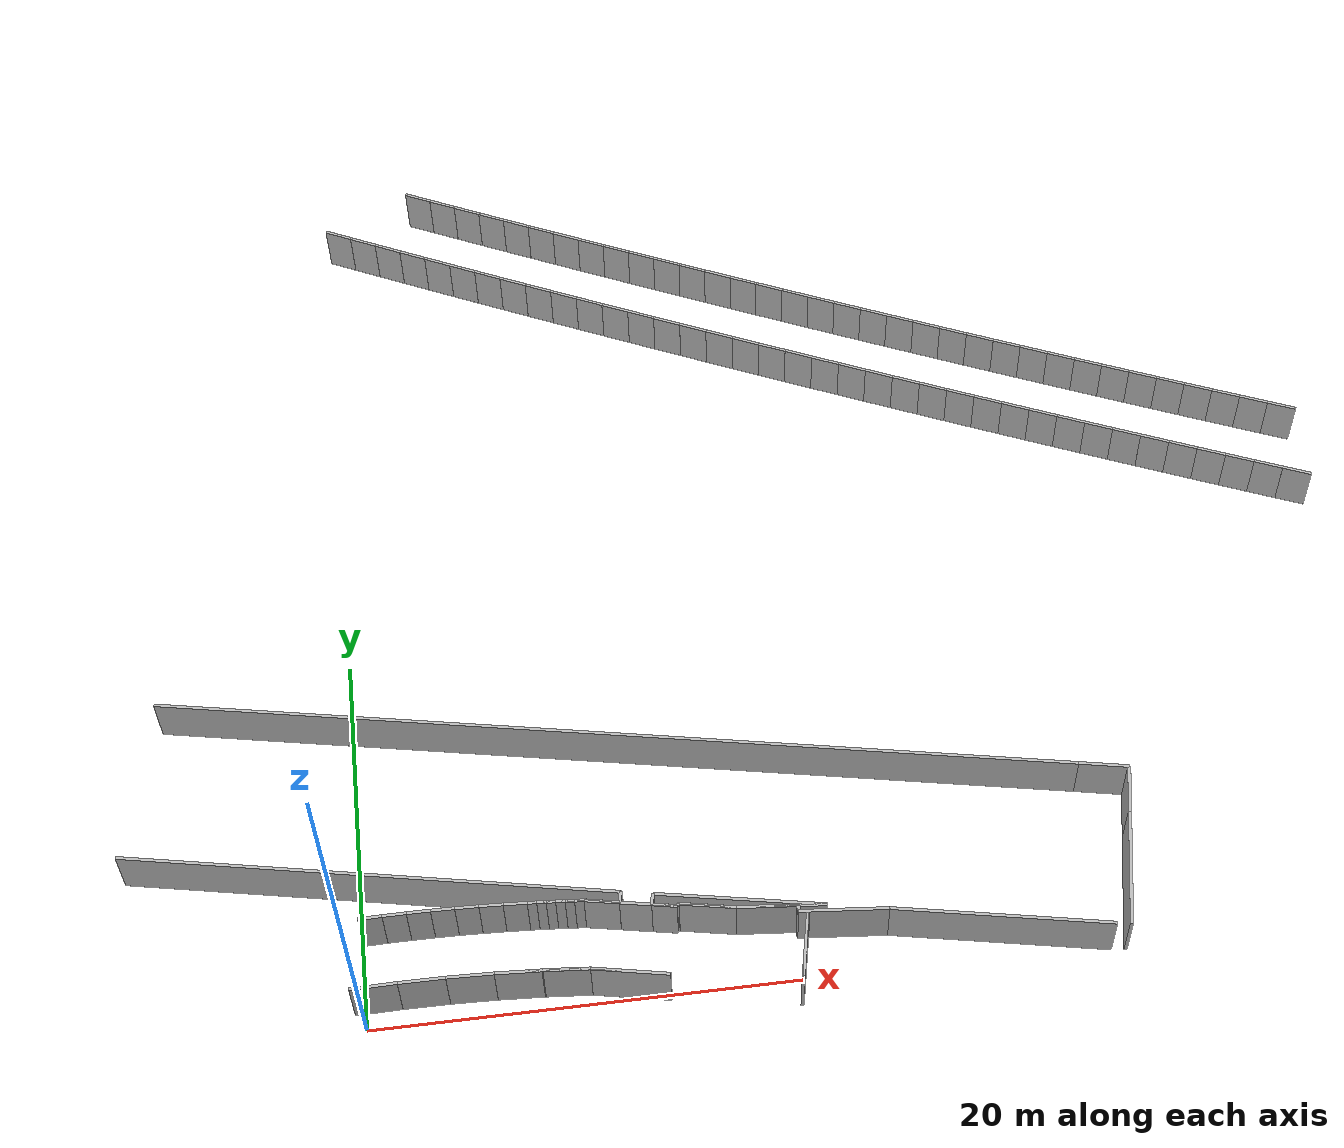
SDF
<?xml version="1.0" ?>
<sdf version="1.6">
  <model name="sps_1405">
    <pose frame="">0 0 0 0 -0 0</pose>
    <static>1</static>
    <self_collide>0</self_collide>
    <allow_auto_disable>0</allow_auto_disable>
    <link name="Wall19">
      <kinematic>0</kinematic>
      <gravity>1</gravity>
      <self_collide>0</self_collide>
      <collision name="collision">
        <geometry>
          <box>
            <size>0.558052 0.15 2.5</size>
          </box>
        </geometry>
        <pose frame="">0 0 0 0 -0 0</pose>
      </collision>
      <visual name="visual">
        <geometry>
          <box>
            <size>0.558052 0.15 2.5</size>
          </box>
        </geometry>
        <pose frame="">0 0 0 0 -0 0</pose>
        <cast_shadows>1</cast_shadows>
        <transparency>0.0</transparency>
      </visual>
      <pose frame="">13.4909 3.71971 1.25 0 -0 1.37308</pose>
    </link>
    <link name="Wall20">
      <kinematic>0</kinematic>
      <gravity>1</gravity>
      <self_collide>0</self_collide>
      <collision name="collision">
        <geometry>
          <box>
            <size>2.70593 0.15 2.5</size>
          </box>
        </geometry>
        <pose frame="">0 0 0 0 -0 0</pose>
      </collision>
      <visual name="visual">
        <geometry>
          <box>
            <size>2.70593 0.15 2.5</size>
          </box>
        </geometry>
        <pose frame="">0 0 0 0 -0 0</pose>
        <cast_shadows>1</cast_shadows>
        <transparency>0.0</transparency>
      </visual>
      <pose frame="">15.9428 3.06648 1.25 0 -0 2.94384</pose>
    </link>
    <link name="Wall21">
      <kinematic>0</kinematic>
      <gravity>1</gravity>
      <self_collide>0</self_collide>
      <collision name="collision">
        <geometry>
          <box>
            <size>0.432153 0.15 2.5</size>
          </box>
        </geometry>
        <pose frame="">0 0 0 0 -0 0</pose>
      </collision>
      <visual name="visual">
        <geometry>
          <box>
            <size>0.432153 0.15 2.5</size>
          </box>
        </geometry>
        <pose frame="">0 0 0 0 -0 0</pose>
        <cast_shadows>1</cast_shadows>
        <transparency>0.0</transparency>
      </visual>
      <pose frame="">20.2974 2.19389 1.25 0 0 -0.199473</pose>
    </link>
    <link name="Wall22">
      <kinematic>0</kinematic>
      <gravity>1</gravity>
      <self_collide>0</self_collide>
      <collision name="collision">
        <geometry>
          <box>
            <size>2.40359 0.15 2.5</size>
          </box>
        </geometry>
        <pose frame="">0 0 0 0 -0 0</pose>
      </collision>
      <visual name="visual">
        <geometry>
          <box>
            <size>2.40359 0.15 2.5</size>
          </box>
        </geometry>
        <pose frame="">0 0 0 0 -0 0</pose>
        <cast_shadows>1</cast_shadows>
        <transparency>0.0</transparency>
      </visual>
      <pose frame="">35.6465 8.17089 1.25 0 -0 2.9385</pose>
    </link>
    <link name="Wall23">
      <kinematic>0</kinematic>
      <gravity>1</gravity>
      <self_collide>0</self_collide>
      <collision name="collision">
        <geometry>
          <box>
            <size>44.7209 0.15 2.5</size>
          </box>
        </geometry>
        <pose frame="">0 0 0 0 -0 0</pose>
      </collision>
      <visual name="visual">
        <geometry>
          <box>
            <size>44.7209 0.15 2.5</size>
          </box>
        </geometry>
        <pose frame="">0 0 0 0 -0 0</pose>
        <cast_shadows>1</cast_shadows>
        <transparency>0.0</transparency>
      </visual>
      <pose frame="">12.5686 12.9235 1.25 0 -0 2.9385</pose>
    </link>
    <link name="Wall26">
      <kinematic>0</kinematic>
      <gravity>1</gravity>
      <self_collide>0</self_collide>
      <collision name="collision">
        <geometry>
          <box>
            <size>10.4229 0.15 2.5</size>
          </box>
        </geometry>
        <pose frame="">0 0 0 0 -0 0</pose>
      </collision>
      <visual name="visual">
        <geometry>
          <box>
            <size>10.4229 0.15 2.5</size>
          </box>
        </geometry>
        <pose frame="">0 0 0 0 -0 0</pose>
        <cast_shadows>1</cast_shadows>
        <transparency>0.0</transparency>
      </visual>
      <pose frame="">29.3646 0.798586 1.25 0 -0 2.93901</pose>
    </link>
    <link name="Wall112">
      <kinematic>0</kinematic>
      <gravity>1</gravity>
      <self_collide>0</self_collide>
      <collision name="collision">
        <geometry>
          <box>
            <size>23.6286 0.15 2.5</size>
          </box>
        </geometry>
        <pose frame="">0 0 0 0 -0 0</pose>
      </collision>
      <visual name="visual">
        <geometry>
          <box>
            <size>23.6286 0.15 2.5</size>
          </box>
        </geometry>
        <pose frame="">0 0 0 0 -0 0</pose>
        <cast_shadows>1</cast_shadows>
        <transparency>0.0</transparency>
      </visual>
      <pose frame="">0.518974 6.69759 1.25 0 -0 2.93608</pose>
    </link>
    <link name="Wall113">
      <kinematic>0</kinematic>
      <gravity>1</gravity>
      <self_collide>0</self_collide>
      <collision name="collision">
        <geometry>
          <box>
            <size>1.18026 0.15 2.5</size>
          </box>
        </geometry>
        <pose frame="">0 0 0 0 -0 0</pose>
      </collision>
      <visual name="visual">
        <geometry>
          <box>
            <size>1.18026 0.15 2.5</size>
          </box>
        </geometry>
        <pose frame="">0 0 0 0 -0 0</pose>
        <cast_shadows>1</cast_shadows>
        <transparency>0.0</transparency>
      </visual>
      <pose frame="">14.0147 3.33009 1.25 0 -0 2.94369</pose>
    </link>
    <link name="Wall114">
      <kinematic>0</kinematic>
      <gravity>1</gravity>
      <self_collide>0</self_collide>
      <collision name="collision">
        <geometry>
          <box>
            <size>4.19215 0.15 2.5</size>
          </box>
        </geometry>
        <pose frame="">0 0 0 0 -0 0</pose>
      </collision>
      <visual name="visual">
        <geometry>
          <box>
            <size>4.19215 0.15 2.5</size>
          </box>
        </geometry>
        <pose frame="">0 0 0 0 -0 0</pose>
        <cast_shadows>1</cast_shadows>
        <transparency>0.0</transparency>
      </visual>
      <pose frame="">22.1727 2.04191 1.25 0 -0 3.04853</pose>
    </link>
    <link name="Wall280">
      <kinematic>0</kinematic>
      <gravity>1</gravity>
      <self_collide>0</self_collide>
      <collision name="collision">
        <geometry>
          <box>
            <size>0.558807 0.15 2.5</size>
          </box>
        </geometry>
        <pose frame="">0 0 0 0 -0 0</pose>
      </collision>
      <visual name="visual">
        <geometry>
          <box>
            <size>0.558807 0.15 2.5</size>
          </box>
        </geometry>
        <pose frame="">0 0 0 0 -0 0</pose>
        <cast_shadows>1</cast_shadows>
        <transparency>0.0</transparency>
      </visual>
      <pose frame="">12.0295 4.0128 1.25 0 -0 1.3719</pose>
    </link>
    <link name="Wall349">
      <kinematic>0</kinematic>
      <gravity>1</gravity>
      <self_collide>0</self_collide>
      <collision name="collision">
        <geometry>
          <box>
            <size>3.64209 0.15 2.5</size>
          </box>
        </geometry>
        <pose frame="">0 0 0 0 -0 0</pose>
      </collision>
      <visual name="visual">
        <geometry>
          <box>
            <size>3.64209 0.15 2.5</size>
          </box>
        </geometry>
        <pose frame="">0 0 0 0 -0 0</pose>
        <cast_shadows>1</cast_shadows>
        <transparency>0.0</transparency>
      </visual>
      <pose frame="">12.1271 0.179488 1.25 0 -0 2.93845</pose>
    </link>
    <link name="Wall429">
      <kinematic>0</kinematic>
      <gravity>1</gravity>
      <self_collide>0</self_collide>
      <collision name="collision">
        <geometry>
          <box>
            <size>1.63883 0.15 2.5</size>
          </box>
        </geometry>
        <pose frame="">0 0 0 0 -0 0</pose>
      </collision>
      <visual name="visual">
        <geometry>
          <box>
            <size>1.63883 0.15 2.5</size>
          </box>
        </geometry>
        <pose frame="">0 0 0 0 -0 0</pose>
        <cast_shadows>1</cast_shadows>
        <transparency>0.0</transparency>
      </visual>
      <pose frame="">11.1709 3.9001 1.25 0 0 -0.198009</pose>
    </link>
    <link name="Wall430">
      <kinematic>0</kinematic>
      <gravity>1</gravity>
      <self_collide>0</self_collide>
      <collision name="collision">
        <geometry>
          <box>
            <size>4.19215 0.15 2.5</size>
          </box>
        </geometry>
        <pose frame="">0 0 0 0 -0 0</pose>
      </collision>
      <visual name="visual">
        <geometry>
          <box>
            <size>4.19215 0.15 2.5</size>
          </box>
        </geometry>
        <pose frame="">0 0 0 0 -0 0</pose>
        <cast_shadows>1</cast_shadows>
        <transparency>0.0</transparency>
      </visual>
      <pose frame="">19.3564 2.60588 1.25 0 -0 3.04853</pose>
    </link>
    <link name="Wall431">
      <kinematic>0</kinematic>
      <gravity>1</gravity>
      <self_collide>0</self_collide>
      <collision name="collision">
        <geometry>
          <box>
            <size>8.0547 0.15 2.5</size>
          </box>
        </geometry>
        <pose frame="">0 0 0 0 -0 0</pose>
      </collision>
      <visual name="visual">
        <geometry>
          <box>
            <size>8.0547 0.15 2.5</size>
          </box>
        </geometry>
        <pose frame="">0 0 0 0 -0 0</pose>
        <cast_shadows>1</cast_shadows>
        <transparency>0.0</transparency>
      </visual>
      <pose frame="">17.4946 3.20219 1.25 0 -0 2.94387</pose>
    </link>
    <link name="Wall524">
      <kinematic>0</kinematic>
      <gravity>1</gravity>
      <self_collide>0</self_collide>
      <collision name="collision">
        <geometry>
          <box>
            <size>3.50128 0.15 2.5</size>
          </box>
        </geometry>
        <pose frame="">0 0 0 0 -0 0</pose>
      </collision>
      <visual name="visual">
        <geometry>
          <box>
            <size>3.50128 0.15 2.5</size>
          </box>
        </geometry>
        <pose frame="">0 0 0 0 -0 0</pose>
        <cast_shadows>1</cast_shadows>
        <transparency>0.0</transparency>
      </visual>
      <pose frame="">20.1558 0.436477 1.25 0 0 -1.77406</pose>
    </link>
    <link name="Wall525">
      <kinematic>0</kinematic>
      <gravity>1</gravity>
      <self_collide>0</self_collide>
      <collision name="collision">
        <geometry>
          <box>
            <size>2.50024 0.15 2.5</size>
          </box>
        </geometry>
        <pose frame="">0 0 0 0 -0 0</pose>
      </collision>
      <visual name="visual">
        <geometry>
          <box>
            <size>2.50024 0.15 2.5</size>
          </box>
        </geometry>
        <pose frame="">0 0 0 0 -0 0</pose>
        <cast_shadows>1</cast_shadows>
        <transparency>0.0</transparency>
      </visual>
      <pose frame="">36.5713 6.70409 1.25 0 -0 1.36759</pose>
    </link>
    <link name="Wall607">
      <kinematic>0</kinematic>
      <gravity>1</gravity>
      <self_collide>0</self_collide>
      <collision name="collision">
        <geometry>
          <box>
            <size>0.120432 0.15 2.5</size>
          </box>
        </geometry>
        <pose frame="">0 0 0 0 -0 0</pose>
      </collision>
      <visual name="visual">
        <geometry>
          <box>
            <size>0.120432 0.15 2.5</size>
          </box>
        </geometry>
        <pose frame="">0 0 0 0 -0 0</pose>
        <cast_shadows>1</cast_shadows>
        <transparency>0.0</transparency>
      </visual>
      <pose frame="">14.6048 3.27318 1.25 0 0 -1.76253</pose>
    </link>
    <link name="Wall993">
      <kinematic>0</kinematic>
      <gravity>1</gravity>
      <self_collide>0</self_collide>
      <collision name="collision">
        <geometry>
          <box>
            <size>5.98487 0.15 2.5</size>
          </box>
        </geometry>
        <pose frame="">0 0 0 0 -0 0</pose>
      </collision>
      <visual name="visual">
        <geometry>
          <box>
            <size>5.98487 0.15 2.5</size>
          </box>
        </geometry>
        <pose frame="">0 0 0 0 -0 0</pose>
        <cast_shadows>1</cast_shadows>
        <transparency>0.0</transparency>
      </visual>
      <pose frame="">35.7154 2.54878 1.25 0 -0 1.36766</pose>
    </link>
    <link name="Wall1701">
      <kinematic>0</kinematic>
      <gravity>1</gravity>
      <self_collide>0</self_collide>
      <collision name="collision">
        <geometry>
          <box>
            <size>1.1106 0.15 2.5</size>
          </box>
        </geometry>
        <pose frame="">0 0 0 0 -0 0</pose>
      </collision>
      <visual name="visual">
        <geometry>
          <box>
            <size>1.1106 0.15 2.5</size>
          </box>
        </geometry>
        <pose frame="">0 0 0 0 -0 0</pose>
        <cast_shadows>1</cast_shadows>
        <transparency>0.0</transparency>
      </visual>
      <pose frame="">0.546867 4.43138 1.25 0 -0 0.0181918</pose>
    </link>
    <link name="Wall1702">
      <kinematic>0</kinematic>
      <gravity>1</gravity>
      <self_collide>0</self_collide>
      <collision name="collision">
        <geometry>
          <box>
            <size>1.11043 0.15 2.5</size>
          </box>
        </geometry>
        <pose frame="">0 0 0 0 -0 0</pose>
      </collision>
      <visual name="visual">
        <geometry>
          <box>
            <size>1.11043 0.15 2.5</size>
          </box>
        </geometry>
        <pose frame="">0 0 0 0 -0 0</pose>
        <cast_shadows>1</cast_shadows>
        <transparency>0.0</transparency>
      </visual>
      <pose frame="">1.65728 4.44459 1.25 0 -0 0.00560649</pose>
    </link>
    <link name="Wall1703">
      <kinematic>0</kinematic>
      <gravity>1</gravity>
      <self_collide>0</self_collide>
      <collision name="collision">
        <geometry>
          <box>
            <size>1.11038 0.15 2.5</size>
          </box>
        </geometry>
        <pose frame="">0 0 0 0 -0 0</pose>
      </collision>
      <visual name="visual">
        <geometry>
          <box>
            <size>1.11038 0.15 2.5</size>
          </box>
        </geometry>
        <pose frame="">0 0 0 0 -0 0</pose>
        <cast_shadows>1</cast_shadows>
        <transparency>0.0</transparency>
      </visual>
      <pose frame="">2.76766 4.44359 1.25 0 0 -0.00742071</pose>
    </link>
    <link name="Wall1704">
      <kinematic>0</kinematic>
      <gravity>1</gravity>
      <self_collide>0</self_collide>
      <collision name="collision">
        <geometry>
          <box>
            <size>1.11063 0.15 2.5</size>
          </box>
        </geometry>
        <pose frame="">0 0 0 0 -0 0</pose>
      </collision>
      <visual name="visual">
        <geometry>
          <box>
            <size>1.11063 0.15 2.5</size>
          </box>
        </geometry>
        <pose frame="">0 0 0 0 -0 0</pose>
        <cast_shadows>1</cast_shadows>
        <transparency>0.0</transparency>
      </visual>
      <pose frame="">3.87804 4.42848 1.25 0 0 -0.0197852</pose>
    </link>
    <link name="Wall1705">
      <kinematic>0</kinematic>
      <gravity>1</gravity>
      <self_collide>0</self_collide>
      <collision name="collision">
        <geometry>
          <box>
            <size>1.11039 0.15 2.5</size>
          </box>
        </geometry>
        <pose frame="">0 0 0 0 -0 0</pose>
      </collision>
      <visual name="visual">
        <geometry>
          <box>
            <size>1.11039 0.15 2.5</size>
          </box>
        </geometry>
        <pose frame="">0 0 0 0 -0 0</pose>
        <cast_shadows>1</cast_shadows>
        <transparency>0.0</transparency>
      </visual>
      <pose frame="">4.98815 4.3994 1.25 0 0 -0.0326013</pose>
    </link>
    <link name="Wall1706">
      <kinematic>0</kinematic>
      <gravity>1</gravity>
      <self_collide>0</self_collide>
      <collision name="collision">
        <geometry>
          <box>
            <size>1.11033 0.15 2.5</size>
          </box>
        </geometry>
        <pose frame="">0 0 0 0 -0 0</pose>
      </collision>
      <visual name="visual">
        <geometry>
          <box>
            <size>1.11033 0.15 2.5</size>
          </box>
        </geometry>
        <pose frame="">0 0 0 0 -0 0</pose>
        <cast_shadows>1</cast_shadows>
        <transparency>0.0</transparency>
      </visual>
      <pose frame="">6.09765 4.35618 1.25 0 0 -0.045256</pose>
    </link>
    <link name="Wall1707">
      <kinematic>0</kinematic>
      <gravity>1</gravity>
      <self_collide>0</self_collide>
      <collision name="collision">
        <geometry>
          <box>
            <size>1.11041 0.15 2.5</size>
          </box>
        </geometry>
        <pose frame="">0 0 0 0 -0 0</pose>
      </collision>
      <visual name="visual">
        <geometry>
          <box>
            <size>1.11041 0.15 2.5</size>
          </box>
        </geometry>
        <pose frame="">0 0 0 0 -0 0</pose>
        <cast_shadows>1</cast_shadows>
        <transparency>0.0</transparency>
      </visual>
      <pose frame="">7.20653 4.29918 1.25 0 0 -0.0574712</pose>
    </link>
    <link name="Wall1708">
      <kinematic>0</kinematic>
      <gravity>1</gravity>
      <self_collide>0</self_collide>
      <collision name="collision">
        <geometry>
          <box>
            <size>0.436024 0.15 2.5</size>
          </box>
        </geometry>
        <pose frame="">0 0 0 0 -0 0</pose>
      </collision>
      <visual name="visual">
        <geometry>
          <box>
            <size>0.436024 0.15 2.5</size>
          </box>
        </geometry>
        <pose frame="">0 0 0 0 -0 0</pose>
        <cast_shadows>1</cast_shadows>
        <transparency>0.0</transparency>
      </visual>
      <pose frame="">7.97835 4.25279 1.25 0 0 -0.0665402</pose>
    </link>
    <link name="Wall1709">
      <kinematic>0</kinematic>
      <gravity>1</gravity>
      <self_collide>0</self_collide>
      <collision name="collision">
        <geometry>
          <box>
            <size>0.435871 0.15 2.5</size>
          </box>
        </geometry>
        <pose frame="">0 0 0 0 -0 0</pose>
      </collision>
      <visual name="visual">
        <geometry>
          <box>
            <size>0.435871 0.15 2.5</size>
          </box>
        </geometry>
        <pose frame="">0 0 0 0 -0 0</pose>
        <cast_shadows>1</cast_shadows>
        <transparency>0.0</transparency>
      </visual>
      <pose frame="">8.41326 4.2227 1.25 0 0 -0.0716167</pose>
    </link>
    <link name="Wall1710">
      <kinematic>0</kinematic>
      <gravity>1</gravity>
      <self_collide>0</self_collide>
      <collision name="collision">
        <geometry>
          <box>
            <size>0.435715 0.15 2.5</size>
          </box>
        </geometry>
        <pose frame="">0 0 0 0 -0 0</pose>
      </collision>
      <visual name="visual">
        <geometry>
          <box>
            <size>0.435715 0.15 2.5</size>
          </box>
        </geometry>
        <pose frame="">0 0 0 0 -0 0</pose>
        <cast_shadows>1</cast_shadows>
        <transparency>0.0</transparency>
      </visual>
      <pose frame="">8.84786 4.1905 1.25 0 0 -0.0762777</pose>
    </link>
    <link name="Wall1711">
      <kinematic>0</kinematic>
      <gravity>1</gravity>
      <self_collide>0</self_collide>
      <collision name="collision">
        <geometry>
          <box>
            <size>0.435827 0.15 2.5</size>
          </box>
        </geometry>
        <pose frame="">0 0 0 0 -0 0</pose>
      </collision>
      <visual name="visual">
        <geometry>
          <box>
            <size>0.435827 0.15 2.5</size>
          </box>
        </geometry>
        <pose frame="">0 0 0 0 -0 0</pose>
        <cast_shadows>1</cast_shadows>
        <transparency>0.0</transparency>
      </visual>
      <pose frame="">9.28228 4.1562 1.25 0 0 -0.0813153</pose>
    </link>
    <link name="Wall1712">
      <kinematic>0</kinematic>
      <gravity>1</gravity>
      <self_collide>0</self_collide>
      <collision name="collision">
        <geometry>
          <box>
            <size>0.435813 0.15 2.5</size>
          </box>
        </geometry>
        <pose frame="">0 0 0 0 -0 0</pose>
      </collision>
      <visual name="visual">
        <geometry>
          <box>
            <size>0.435813 0.15 2.5</size>
          </box>
        </geometry>
        <pose frame="">0 0 0 0 -0 0</pose>
        <cast_shadows>1</cast_shadows>
        <transparency>0.0</transparency>
      </visual>
      <pose frame="">9.71657 4.1198 1.25 0 0 -0.0859558</pose>
    </link>
    <link name="Wall1713">
      <kinematic>0</kinematic>
      <gravity>1</gravity>
      <self_collide>0</self_collide>
      <collision name="collision">
        <geometry>
          <box>
            <size>0.435781 0.15 2.5</size>
          </box>
        </geometry>
        <pose frame="">0 0 0 0 -0 0</pose>
      </collision>
      <visual name="visual">
        <geometry>
          <box>
            <size>0.435781 0.15 2.5</size>
          </box>
        </geometry>
        <pose frame="">0 0 0 0 -0 0</pose>
        <cast_shadows>1</cast_shadows>
        <transparency>0.0</transparency>
      </visual>
      <pose frame="">10.1507 4.08119 1.25 0 0 -0.0914461</pose>
    </link>
    <link name="Wall1714">
      <kinematic>0</kinematic>
      <gravity>1</gravity>
      <self_collide>0</self_collide>
      <collision name="collision">
        <geometry>
          <box>
            <size>1.63901 0.15 2.5</size>
          </box>
        </geometry>
        <pose frame="">0 0 0 0 -0 0</pose>
      </collision>
      <visual name="visual">
        <geometry>
          <box>
            <size>1.63901 0.15 2.5</size>
          </box>
        </geometry>
        <pose frame="">0 0 0 0 -0 0</pose>
        <cast_shadows>1</cast_shadows>
        <transparency>0.0</transparency>
      </visual>
      <pose frame="">11.1711 3.9001 1.25 0 0 -0.197987</pose>
    </link>
    <link name="Wall1715">
      <kinematic>0</kinematic>
      <gravity>1</gravity>
      <self_collide>0</self_collide>
      <collision name="collision">
        <geometry>
          <box>
            <size>1.49061 0.15 2.5</size>
          </box>
        </geometry>
        <pose frame="">0 0 0 0 -0 0</pose>
      </collision>
      <visual name="visual">
        <geometry>
          <box>
            <size>1.49061 0.15 2.5</size>
          </box>
        </geometry>
        <pose frame="">0 0 0 0 -0 0</pose>
        <cast_shadows>1</cast_shadows>
        <transparency>0.0</transparency>
      </visual>
      <pose frame="">12.7054 3.5926 1.25 0 0 -0.19758</pose>
    </link>
    <link name="Wall1716">
      <kinematic>0</kinematic>
      <gravity>1</gravity>
      <self_collide>0</self_collide>
      <collision name="collision">
        <geometry>
          <box>
            <size>1.1803 0.15 2.5</size>
          </box>
        </geometry>
        <pose frame="">0 0 0 0 -0 0</pose>
      </collision>
      <visual name="visual">
        <geometry>
          <box>
            <size>1.1803 0.15 2.5</size>
          </box>
        </geometry>
        <pose frame="">0 0 0 0 -0 0</pose>
        <cast_shadows>1</cast_shadows>
        <transparency>0.0</transparency>
      </visual>
      <pose frame="">14.0149 3.33018 1.25 0 0 -0.198055</pose>
    </link>
    <link name="Wall1717">
      <kinematic>0</kinematic>
      <gravity>1</gravity>
      <self_collide>0</self_collide>
      <collision name="collision">
        <geometry>
          <box>
            <size>0.120623 0.15 2.5</size>
          </box>
        </geometry>
        <pose frame="">0 0 0 0 -0 0</pose>
      </collision>
      <visual name="visual">
        <geometry>
          <box>
            <size>0.120623 0.15 2.5</size>
          </box>
        </geometry>
        <pose frame="">0 0 0 0 -0 0</pose>
        <cast_shadows>1</cast_shadows>
        <transparency>0.0</transparency>
      </visual>
      <pose frame="">14.605 3.27327 1.25 0 -0 1.37886</pose>
    </link>
    <link name="Wall1718">
      <kinematic>0</kinematic>
      <gravity>1</gravity>
      <self_collide>0</self_collide>
      <collision name="collision">
        <geometry>
          <box>
            <size>2.70597 0.15 2.5</size>
          </box>
        </geometry>
        <pose frame="">0 0 0 0 -0 0</pose>
      </collision>
      <visual name="visual">
        <geometry>
          <box>
            <size>2.70597 0.15 2.5</size>
          </box>
        </geometry>
        <pose frame="">0 0 0 0 -0 0</pose>
        <cast_shadows>1</cast_shadows>
        <transparency>0.0</transparency>
      </visual>
      <pose frame="">15.9431 3.06657 1.25 0 0 -0.197816</pose>
    </link>
    <link name="Wall1719">
      <kinematic>0</kinematic>
      <gravity>1</gravity>
      <self_collide>0</self_collide>
      <collision name="collision">
        <geometry>
          <box>
            <size>2.85635 0.15 2.5</size>
          </box>
        </geometry>
        <pose frame="">0 0 0 0 -0 0</pose>
      </collision>
      <visual name="visual">
        <geometry>
          <box>
            <size>2.85635 0.15 2.5</size>
          </box>
        </geometry>
        <pose frame="">0 0 0 0 -0 0</pose>
        <cast_shadows>1</cast_shadows>
        <transparency>0.0</transparency>
      </visual>
      <pose frame="">18.6917 2.66798 1.25 0 0 -0.0930433</pose>
    </link>
    <link name="Wall1720">
      <kinematic>0</kinematic>
      <gravity>1</gravity>
      <self_collide>0</self_collide>
      <collision name="collision">
        <geometry>
          <box>
            <size>0.299878 0.15 2.5</size>
          </box>
        </geometry>
        <pose frame="">0 0 0 0 -0 0</pose>
      </collision>
      <visual name="visual">
        <geometry>
          <box>
            <size>0.299878 0.15 2.5</size>
          </box>
        </geometry>
        <pose frame="">0 0 0 0 -0 0</pose>
        <cast_shadows>1</cast_shadows>
        <transparency>0.0</transparency>
      </visual>
      <pose frame="">20.0998 2.386 1.25 0 0 -1.66374</pose>
    </link>
    <link name="Wall1721">
      <kinematic>0</kinematic>
      <gravity>1</gravity>
      <self_collide>0</self_collide>
      <collision name="collision">
        <geometry>
          <box>
            <size>0.432213 0.15 2.5</size>
          </box>
        </geometry>
        <pose frame="">0 0 0 0 -0 0</pose>
      </collision>
      <visual name="visual">
        <geometry>
          <box>
            <size>0.432213 0.15 2.5</size>
          </box>
        </geometry>
        <pose frame="">0 0 0 0 -0 0</pose>
        <cast_shadows>1</cast_shadows>
        <transparency>0.0</transparency>
      </visual>
      <pose frame="">20.2977 2.19389 1.25 0 0 -0.199445</pose>
    </link>
    <link name="Wall1722">
      <kinematic>0</kinematic>
      <gravity>1</gravity>
      <self_collide>0</self_collide>
      <collision name="collision">
        <geometry>
          <box>
            <size>3.50124 0.15 2.5</size>
          </box>
        </geometry>
        <pose frame="">0 0 0 0 -0 0</pose>
      </collision>
      <visual name="visual">
        <geometry>
          <box>
            <size>3.50124 0.15 2.5</size>
          </box>
        </geometry>
        <pose frame="">0 0 0 0 -0 0</pose>
        <cast_shadows>1</cast_shadows>
        <transparency>0.0</transparency>
      </visual>
      <pose frame="">20.1562 0.436477 1.25 0 0 -1.77401</pose>
    </link>
    <link name="Wall1725">
      <kinematic>0</kinematic>
      <gravity>1</gravity>
      <self_collide>0</self_collide>
      <collision name="collision">
        <geometry>
          <box>
            <size>3.64191 0.15 2.5</size>
          </box>
        </geometry>
        <pose frame="">0 0 0 0 -0 0</pose>
      </collision>
      <visual name="visual">
        <geometry>
          <box>
            <size>3.64191 0.15 2.5</size>
          </box>
        </geometry>
        <pose frame="">0 0 0 0 -0 0</pose>
        <cast_shadows>1</cast_shadows>
        <transparency>0.0</transparency>
      </visual>
      <pose frame="">12.1273 0.179488 1.25 0 -0 2.93844</pose>
    </link>
    <link name="Wall1726">
      <kinematic>0</kinematic>
      <gravity>1</gravity>
      <self_collide>0</self_collide>
      <collision name="collision">
        <geometry>
          <box>
            <size>2.18198 0.15 2.5</size>
          </box>
        </geometry>
        <pose frame="">0 0 0 0 -0 0</pose>
      </collision>
      <visual name="visual">
        <geometry>
          <box>
            <size>2.18198 0.15 2.5</size>
          </box>
        </geometry>
        <pose frame="">0 0 0 0 -0 0</pose>
        <cast_shadows>1</cast_shadows>
        <transparency>0.0</transparency>
      </visual>
      <pose frame="">9.25674 0.638991 1.25 0 -0 3.05707</pose>
    </link>
    <link name="Wall1727">
      <kinematic>0</kinematic>
      <gravity>1</gravity>
      <self_collide>0</self_collide>
      <collision name="collision">
        <geometry>
          <box>
            <size>2.18191 0.15 2.5</size>
          </box>
        </geometry>
        <pose frame="">0 0 0 0 -0 0</pose>
      </collision>
      <visual name="visual">
        <geometry>
          <box>
            <size>2.18191 0.15 2.5</size>
          </box>
        </geometry>
        <pose frame="">0 0 0 0 -0 0</pose>
        <cast_shadows>1</cast_shadows>
        <transparency>0.0</transparency>
      </visual>
      <pose frame="">7.08056 0.794997 1.25 0 -0 3.08298</pose>
    </link>
    <link name="Wall1728">
      <kinematic>0</kinematic>
      <gravity>1</gravity>
      <self_collide>0</self_collide>
      <collision name="collision">
        <geometry>
          <box>
            <size>2.18202 0.15 2.5</size>
          </box>
        </geometry>
        <pose frame="">0 0 0 0 -0 0</pose>
      </collision>
      <visual name="visual">
        <geometry>
          <box>
            <size>2.18202 0.15 2.5</size>
          </box>
        </geometry>
        <pose frame="">0 0 0 0 -0 0</pose>
        <cast_shadows>1</cast_shadows>
        <transparency>0.0</transparency>
      </visual>
      <pose frame="">4.90105 0.894698 1.25 0 -0 3.10878</pose>
    </link>
    <link name="Wall1729">
      <kinematic>0</kinematic>
      <gravity>1</gravity>
      <self_collide>0</self_collide>
      <collision name="collision">
        <geometry>
          <box>
            <size>2.18182 0.15 2.5</size>
          </box>
        </geometry>
        <pose frame="">0 0 0 0 -0 0</pose>
      </collision>
      <visual name="visual">
        <geometry>
          <box>
            <size>2.18182 0.15 2.5</size>
          </box>
        </geometry>
        <pose frame="">0 0 0 0 -0 0</pose>
        <cast_shadows>1</cast_shadows>
        <transparency>0.0</transparency>
      </visual>
      <pose frame="">2.71975 0.938094 1.25 0 -0 3.13463</pose>
    </link>
    <link name="Wall1730">
      <kinematic>0</kinematic>
      <gravity>1</gravity>
      <self_collide>0</self_collide>
      <collision name="collision">
        <geometry>
          <box>
            <size>2.18203 0.15 2.5</size>
          </box>
        </geometry>
        <pose frame="">0 0 0 0 -0 0</pose>
      </collision>
      <visual name="visual">
        <geometry>
          <box>
            <size>2.18203 0.15 2.5</size>
          </box>
        </geometry>
        <pose frame="">0 0 0 0 -0 0</pose>
        <cast_shadows>1</cast_shadows>
        <transparency>0.0</transparency>
      </visual>
      <pose frame="">0.538047 0.925094 1.25 0 0 -3.12271</pose>
    </link>
    <link name="Wall2688">
      <kinematic>0</kinematic>
      <gravity>1</gravity>
      <self_collide>0</self_collide>
      <collision name="collision">
        <geometry>
          <box>
            <size>0.469425 0.15 2.5</size>
          </box>
        </geometry>
        <pose frame="">0 0 0 0 -0 0</pose>
      </collision>
      <visual name="visual">
        <geometry>
          <box>
            <size>0.469425 0.15 2.5</size>
          </box>
        </geometry>
        <pose frame="">0 0 0 0 -0 0</pose>
        <cast_shadows>1</cast_shadows>
        <transparency>0.0</transparency>
      </visual>
      <pose frame="">7.76986 0.758498 1.25 0 0 -0.0666201</pose>
    </link>
    <link name="Wall2689">
      <kinematic>0</kinematic>
      <gravity>1</gravity>
      <self_collide>0</self_collide>
      <collision name="collision">
        <geometry>
          <box>
            <size>0.469616 0.15 2.5</size>
          </box>
        </geometry>
        <pose frame="">0 0 0 0 -0 0</pose>
      </collision>
      <visual name="visual">
        <geometry>
          <box>
            <size>0.469616 0.15 2.5</size>
          </box>
        </geometry>
        <pose frame="">0 0 0 0 -0 0</pose>
        <cast_shadows>1</cast_shadows>
        <transparency>0.0</transparency>
      </visual>
      <pose frame="">8.23824 0.725875 1.25 0 0 -0.0724557</pose>
    </link>
    <link name="Wall2690">
      <kinematic>0</kinematic>
      <gravity>1</gravity>
      <self_collide>0</self_collide>
      <collision name="collision">
        <geometry>
          <box>
            <size>0.469443 0.15 2.5</size>
          </box>
        </geometry>
        <pose frame="">0 0 0 0 -0 0</pose>
      </collision>
      <visual name="visual">
        <geometry>
          <box>
            <size>0.469443 0.15 2.5</size>
          </box>
        </geometry>
        <pose frame="">0 0 0 0 -0 0</pose>
        <cast_shadows>1</cast_shadows>
        <transparency>0.0</transparency>
      </visual>
      <pose frame="">8.70644 0.690596 1.25 0 0 -0.0779585</pose>
    </link>
    <link name="Wall2691">
      <kinematic>0</kinematic>
      <gravity>1</gravity>
      <self_collide>0</self_collide>
      <collision name="collision">
        <geometry>
          <box>
            <size>0.469417 0.15 2.5</size>
          </box>
        </geometry>
        <pose frame="">0 0 0 0 -0 0</pose>
      </collision>
      <visual name="visual">
        <geometry>
          <box>
            <size>0.469417 0.15 2.5</size>
          </box>
        </geometry>
        <pose frame="">0 0 0 0 -0 0</pose>
        <cast_shadows>1</cast_shadows>
        <transparency>0.0</transparency>
      </visual>
      <pose frame="">9.17434 0.652694 1.25 0 0 -0.0837027</pose>
    </link>
    <link name="Wall2692">
      <kinematic>0</kinematic>
      <gravity>1</gravity>
      <self_collide>0</self_collide>
      <collision name="collision">
        <geometry>
          <box>
            <size>0.469715 0.15 2.5</size>
          </box>
        </geometry>
        <pose frame="">0 0 0 0 -0 0</pose>
      </collision>
      <visual name="visual">
        <geometry>
          <box>
            <size>0.469715 0.15 2.5</size>
          </box>
        </geometry>
        <pose frame="">0 0 0 0 -0 0</pose>
        <cast_shadows>1</cast_shadows>
        <transparency>0.0</transparency>
      </visual>
      <pose frame="">9.64214 0.612075 1.25 0 0 -0.0895188</pose>
    </link>
    <link name="Wall2693">
      <kinematic>0</kinematic>
      <gravity>1</gravity>
      <self_collide>0</self_collide>
      <collision name="collision">
        <geometry>
          <box>
            <size>0.469491 0.15 2.5</size>
          </box>
        </geometry>
        <pose frame="">0 0 0 0 -0 0</pose>
      </collision>
      <visual name="visual">
        <geometry>
          <box>
            <size>0.469491 0.15 2.5</size>
          </box>
        </geometry>
        <pose frame="">0 0 0 0 -0 0</pose>
        <cast_shadows>1</cast_shadows>
        <transparency>0.0</transparency>
      </visual>
      <pose frame="">10.1098 0.568984 1.25 0 0 -0.0942615</pose>
    </link>
    <link name="Wall3531">
      <kinematic>0</kinematic>
      <gravity>1</gravity>
      <self_collide>0</self_collide>
      <collision name="collision">
        <geometry>
          <box>
            <size>0.43595 0.15 2.5</size>
          </box>
        </geometry>
        <pose frame="">0 0 0 0 -0 0</pose>
      </collision>
      <visual name="visual">
        <geometry>
          <box>
            <size>0.43595 0.15 2.5</size>
          </box>
        </geometry>
        <pose frame="">0 0 0 0 -0 0</pose>
        <cast_shadows>1</cast_shadows>
        <transparency>0.0</transparency>
      </visual>
      <pose frame="">7.97814 4.2527 1.25 0 0 -0.0661305</pose>
    </link>
    <link name="Wall3532">
      <kinematic>0</kinematic>
      <gravity>1</gravity>
      <self_collide>0</self_collide>
      <collision name="collision">
        <geometry>
          <box>
            <size>0.435749 0.15 2.5</size>
          </box>
        </geometry>
        <pose frame="">0 0 0 0 -0 0</pose>
      </collision>
      <visual name="visual">
        <geometry>
          <box>
            <size>0.435749 0.15 2.5</size>
          </box>
        </geometry>
        <pose frame="">0 0 0 0 -0 0</pose>
        <cast_shadows>1</cast_shadows>
        <transparency>0.0</transparency>
      </visual>
      <pose frame="">8.41296 4.2227 1.25 0 0 -0.0716368</pose>
    </link>
    <link name="Wall3533">
      <kinematic>0</kinematic>
      <gravity>1</gravity>
      <self_collide>0</self_collide>
      <collision name="collision">
        <geometry>
          <box>
            <size>0.435837 0.15 2.5</size>
          </box>
        </geometry>
        <pose frame="">0 0 0 0 -0 0</pose>
      </collision>
      <visual name="visual">
        <geometry>
          <box>
            <size>0.435837 0.15 2.5</size>
          </box>
        </geometry>
        <pose frame="">0 0 0 0 -0 0</pose>
        <cast_shadows>1</cast_shadows>
        <transparency>0.0</transparency>
      </visual>
      <pose frame="">8.84756 4.1905 1.25 0 0 -0.0762563</pose>
    </link>
    <link name="Wall3534">
      <kinematic>0</kinematic>
      <gravity>1</gravity>
      <self_collide>0</self_collide>
      <collision name="collision">
        <geometry>
          <box>
            <size>0.435827 0.15 2.5</size>
          </box>
        </geometry>
        <pose frame="">0 0 0 0 -0 0</pose>
      </collision>
      <visual name="visual">
        <geometry>
          <box>
            <size>0.435827 0.15 2.5</size>
          </box>
        </geometry>
        <pose frame="">0 0 0 0 -0 0</pose>
        <cast_shadows>1</cast_shadows>
        <transparency>0.0</transparency>
      </visual>
      <pose frame="">9.28204 4.1562 1.25 0 0 -0.0813153</pose>
    </link>
    <link name="Wall3535">
      <kinematic>0</kinematic>
      <gravity>1</gravity>
      <self_collide>0</self_collide>
      <collision name="collision">
        <geometry>
          <box>
            <size>0.435829 0.15 2.5</size>
          </box>
        </geometry>
        <pose frame="">0 0 0 0 -0 0</pose>
      </collision>
      <visual name="visual">
        <geometry>
          <box>
            <size>0.435829 0.15 2.5</size>
          </box>
        </geometry>
        <pose frame="">0 0 0 0 -0 0</pose>
        <cast_shadows>1</cast_shadows>
        <transparency>0.0</transparency>
      </visual>
      <pose frame="">9.71633 4.1197 1.25 0 0 -0.0863744</pose>
    </link>
    <link name="Wall3536">
      <kinematic>0</kinematic>
      <gravity>1</gravity>
      <self_collide>0</self_collide>
      <collision name="collision">
        <geometry>
          <box>
            <size>0.435825 0.15 2.5</size>
          </box>
        </geometry>
        <pose frame="">0 0 0 0 -0 0</pose>
      </collision>
      <visual name="visual">
        <geometry>
          <box>
            <size>0.435825 0.15 2.5</size>
          </box>
        </geometry>
        <pose frame="">0 0 0 0 -0 0</pose>
        <cast_shadows>1</cast_shadows>
        <transparency>0.0</transparency>
      </visual>
      <pose frame="">10.1504 4.0811 1.25 0 0 -0.0910149</pose>
    </link>
    <link name="Wall8710">
      <kinematic>0</kinematic>
      <gravity>1</gravity>
      <self_collide>0</self_collide>
      <collision name="collision">
        <geometry>
          <box>
            <size>1.49888 0.15 2.5</size>
          </box>
        </geometry>
        <pose frame="">0 0 0 0 -0 0</pose>
      </collision>
      <visual name="visual">
        <geometry>
          <box>
            <size>1.49888 0.15 2.5</size>
          </box>
        </geometry>
        <pose frame="">0 0 0 0 -0 0</pose>
        <cast_shadows>1</cast_shadows>
        <transparency>0.0</transparency>
      </visual>
      <pose frame="">0.674766 47.654 1.25 0 0 -0.473117</pose>
    </link>
    <link name="Wall8711">
      <kinematic>0</kinematic>
      <gravity>1</gravity>
      <self_collide>0</self_collide>
      <collision name="collision">
        <geometry>
          <box>
            <size>1.49894 0.15 2.5</size>
          </box>
        </geometry>
        <pose frame="">0 0 0 0 -0 0</pose>
      </collision>
      <visual name="visual">
        <geometry>
          <box>
            <size>1.49894 0.15 2.5</size>
          </box>
        </geometry>
        <pose frame="">0 0 0 0 -0 0</pose>
        <cast_shadows>1</cast_shadows>
        <transparency>0.0</transparency>
      </visual>
      <pose frame="">2.00957 46.9721 1.25 0 0 -0.471496</pose>
    </link>
    <link name="Wall8712">
      <kinematic>0</kinematic>
      <gravity>1</gravity>
      <self_collide>0</self_collide>
      <collision name="collision">
        <geometry>
          <box>
            <size>1.49895 0.15 2.5</size>
          </box>
        </geometry>
        <pose frame="">0 0 0 0 -0 0</pose>
      </collision>
      <visual name="visual">
        <geometry>
          <box>
            <size>1.49895 0.15 2.5</size>
          </box>
        </geometry>
        <pose frame="">0 0 0 0 -0 0</pose>
        <cast_shadows>1</cast_shadows>
        <transparency>0.0</transparency>
      </visual>
      <pose frame="">3.34545 46.2922 1.25 0 0 -0.470076</pose>
    </link>
    <link name="Wall8713">
      <kinematic>0</kinematic>
      <gravity>1</gravity>
      <self_collide>0</self_collide>
      <collision name="collision">
        <geometry>
          <box>
            <size>1.49904 0.15 2.5</size>
          </box>
        </geometry>
        <pose frame="">0 0 0 0 -0 0</pose>
      </collision>
      <visual name="visual">
        <geometry>
          <box>
            <size>1.49904 0.15 2.5</size>
          </box>
        </geometry>
        <pose frame="">0 0 0 0 -0 0</pose>
        <cast_shadows>1</cast_shadows>
        <transparency>0.0</transparency>
      </visual>
      <pose frame="">4.68246 45.6144 1.25 0 0 -0.468309</pose>
    </link>
    <link name="Wall8714">
      <kinematic>0</kinematic>
      <gravity>1</gravity>
      <self_collide>0</self_collide>
      <collision name="collision">
        <geometry>
          <box>
            <size>1.49893 0.15 2.5</size>
          </box>
        </geometry>
        <pose frame="">0 0 0 0 -0 0</pose>
      </collision>
      <visual name="visual">
        <geometry>
          <box>
            <size>1.49893 0.15 2.5</size>
          </box>
        </geometry>
        <pose frame="">0 0 0 0 -0 0</pose>
        <cast_shadows>1</cast_shadows>
        <transparency>0.0</transparency>
      </visual>
      <pose frame="">6.02056 44.9388 1.25 0 0 -0.466798</pose>
    </link>
    <link name="Wall8715">
      <kinematic>0</kinematic>
      <gravity>1</gravity>
      <self_collide>0</self_collide>
      <collision name="collision">
        <geometry>
          <box>
            <size>1.49889 0.15 2.5</size>
          </box>
        </geometry>
        <pose frame="">0 0 0 0 -0 0</pose>
      </collision>
      <visual name="visual">
        <geometry>
          <box>
            <size>1.49889 0.15 2.5</size>
          </box>
        </geometry>
        <pose frame="">0 0 0 0 -0 0</pose>
        <cast_shadows>1</cast_shadows>
        <transparency>0.0</transparency>
      </visual>
      <pose frame="">7.35964 44.2653 1.25 0 0 -0.465214</pose>
    </link>
    <link name="Wall8716">
      <kinematic>0</kinematic>
      <gravity>1</gravity>
      <self_collide>0</self_collide>
      <collision name="collision">
        <geometry>
          <box>
            <size>1.49908 0.15 2.5</size>
          </box>
        </geometry>
        <pose frame="">0 0 0 0 -0 0</pose>
      </collision>
      <visual name="visual">
        <geometry>
          <box>
            <size>1.49908 0.15 2.5</size>
          </box>
        </geometry>
        <pose frame="">0 0 0 0 -0 0</pose>
        <cast_shadows>1</cast_shadows>
        <transparency>0.0</transparency>
      </visual>
      <pose frame="">8.69985 43.5939 1.25 0 0 -0.463648</pose>
    </link>
    <link name="Wall8717">
      <kinematic>0</kinematic>
      <gravity>1</gravity>
      <self_collide>0</self_collide>
      <collision name="collision">
        <geometry>
          <box>
            <size>1.49887 0.15 2.5</size>
          </box>
        </geometry>
        <pose frame="">0 0 0 0 -0 0</pose>
      </collision>
      <visual name="visual">
        <geometry>
          <box>
            <size>1.49887 0.15 2.5</size>
          </box>
        </geometry>
        <pose frame="">0 0 0 0 -0 0</pose>
        <cast_shadows>1</cast_shadows>
        <transparency>0.0</transparency>
      </visual>
      <pose frame="">10.0412 42.9247 1.25 0 0 -0.461899</pose>
    </link>
    <link name="Wall8718">
      <kinematic>0</kinematic>
      <gravity>1</gravity>
      <self_collide>0</self_collide>
      <collision name="collision">
        <geometry>
          <box>
            <size>1.49887 0.15 2.5</size>
          </box>
        </geometry>
        <pose frame="">0 0 0 0 -0 0</pose>
      </collision>
      <visual name="visual">
        <geometry>
          <box>
            <size>1.49887 0.15 2.5</size>
          </box>
        </geometry>
        <pose frame="">0 0 0 0 -0 0</pose>
        <cast_shadows>1</cast_shadows>
        <transparency>0.0</transparency>
      </visual>
      <pose frame="">11.3834 42.2577 1.25 0 0 -0.460442</pose>
    </link>
    <link name="Wall8719">
      <kinematic>0</kinematic>
      <gravity>1</gravity>
      <self_collide>0</self_collide>
      <collision name="collision">
        <geometry>
          <box>
            <size>1.49891 0.15 2.5</size>
          </box>
        </geometry>
        <pose frame="">0 0 0 0 -0 0</pose>
      </collision>
      <visual name="visual">
        <geometry>
          <box>
            <size>1.49891 0.15 2.5</size>
          </box>
        </geometry>
        <pose frame="">0 0 0 0 -0 0</pose>
        <cast_shadows>1</cast_shadows>
        <transparency>0.0</transparency>
      </visual>
      <pose frame="">12.7267 41.5927 1.25 0 0 -0.458931</pose>
    </link>
    <link name="Wall8720">
      <kinematic>0</kinematic>
      <gravity>1</gravity>
      <self_collide>0</self_collide>
      <collision name="collision">
        <geometry>
          <box>
            <size>1.49903 0.15 2.5</size>
          </box>
        </geometry>
        <pose frame="">0 0 0 0 -0 0</pose>
      </collision>
      <visual name="visual">
        <geometry>
          <box>
            <size>1.49903 0.15 2.5</size>
          </box>
        </geometry>
        <pose frame="">0 0 0 0 -0 0</pose>
        <cast_shadows>1</cast_shadows>
        <transparency>0.0</transparency>
      </visual>
      <pose frame="">14.0712 40.9298 1.25 0 0 -0.457256</pose>
    </link>
    <link name="Wall8721">
      <kinematic>0</kinematic>
      <gravity>1</gravity>
      <self_collide>0</self_collide>
      <collision name="collision">
        <geometry>
          <box>
            <size>1.49894 0.15 2.5</size>
          </box>
        </geometry>
        <pose frame="">0 0 0 0 -0 0</pose>
      </collision>
      <visual name="visual">
        <geometry>
          <box>
            <size>1.49894 0.15 2.5</size>
          </box>
        </geometry>
        <pose frame="">0 0 0 0 -0 0</pose>
        <cast_shadows>1</cast_shadows>
        <transparency>0.0</transparency>
      </visual>
      <pose frame="">15.4167 40.2691 1.25 0 0 -0.455653</pose>
    </link>
    <link name="Wall8722">
      <kinematic>0</kinematic>
      <gravity>1</gravity>
      <self_collide>0</self_collide>
      <collision name="collision">
        <geometry>
          <box>
            <size>1.4991 0.15 2.5</size>
          </box>
        </geometry>
        <pose frame="">0 0 0 0 -0 0</pose>
      </collision>
      <visual name="visual">
        <geometry>
          <box>
            <size>1.4991 0.15 2.5</size>
          </box>
        </geometry>
        <pose frame="">0 0 0 0 -0 0</pose>
        <cast_shadows>1</cast_shadows>
        <transparency>0.0</transparency>
      </visual>
      <pose frame="">16.7633 39.6105 1.25 0 0 -0.454106</pose>
    </link>
    <link name="Wall8723">
      <kinematic>0</kinematic>
      <gravity>1</gravity>
      <self_collide>0</self_collide>
      <collision name="collision">
        <geometry>
          <box>
            <size>1.49876 0.15 2.5</size>
          </box>
        </geometry>
        <pose frame="">0 0 0 0 -0 0</pose>
      </collision>
      <visual name="visual">
        <geometry>
          <box>
            <size>1.49876 0.15 2.5</size>
          </box>
        </geometry>
        <pose frame="">0 0 0 0 -0 0</pose>
        <cast_shadows>1</cast_shadows>
        <transparency>0.0</transparency>
      </visual>
      <pose frame="">18.1107 38.9539 1.25 0 0 -0.45272</pose>
    </link>
    <link name="Wall8724">
      <kinematic>0</kinematic>
      <gravity>1</gravity>
      <self_collide>0</self_collide>
      <collision name="collision">
        <geometry>
          <box>
            <size>1.49904 0.15 2.5</size>
          </box>
        </geometry>
        <pose frame="">0 0 0 0 -0 0</pose>
      </collision>
      <visual name="visual">
        <geometry>
          <box>
            <size>1.49904 0.15 2.5</size>
          </box>
        </geometry>
        <pose frame="">0 0 0 0 -0 0</pose>
        <cast_shadows>1</cast_shadows>
        <transparency>0.0</transparency>
      </visual>
      <pose frame="">19.4593 38.2995 1.25 0 0 -0.450865</pose>
    </link>
    <link name="Wall8725">
      <kinematic>0</kinematic>
      <gravity>1</gravity>
      <self_collide>0</self_collide>
      <collision name="collision">
        <geometry>
          <box>
            <size>1.49885 0.15 2.5</size>
          </box>
        </geometry>
        <pose frame="">0 0 0 0 -0 0</pose>
      </collision>
      <visual name="visual">
        <geometry>
          <box>
            <size>1.49885 0.15 2.5</size>
          </box>
        </geometry>
        <pose frame="">0 0 0 0 -0 0</pose>
        <cast_shadows>1</cast_shadows>
        <transparency>0.0</transparency>
      </visual>
      <pose frame="">20.8089 37.6473 1.25 0 0 -0.449479</pose>
    </link>
    <link name="Wall8726">
      <kinematic>0</kinematic>
      <gravity>1</gravity>
      <self_collide>0</self_collide>
      <collision name="collision">
        <geometry>
          <box>
            <size>1.49897 0.15 2.5</size>
          </box>
        </geometry>
        <pose frame="">0 0 0 0 -0 0</pose>
      </collision>
      <visual name="visual">
        <geometry>
          <box>
            <size>1.49897 0.15 2.5</size>
          </box>
        </geometry>
        <pose frame="">0 0 0 0 -0 0</pose>
        <cast_shadows>1</cast_shadows>
        <transparency>0.0</transparency>
      </visual>
      <pose frame="">22.1594 36.9972 1.25 0 0 -0.447768</pose>
    </link>
    <link name="Wall8727">
      <kinematic>0</kinematic>
      <gravity>1</gravity>
      <self_collide>0</self_collide>
      <collision name="collision">
        <geometry>
          <box>
            <size>1.49904 0.15 2.5</size>
          </box>
        </geometry>
        <pose frame="">0 0 0 0 -0 0</pose>
      </collision>
      <visual name="visual">
        <geometry>
          <box>
            <size>1.49904 0.15 2.5</size>
          </box>
        </geometry>
        <pose frame="">0 0 0 0 -0 0</pose>
        <cast_shadows>1</cast_shadows>
        <transparency>0.0</transparency>
      </visual>
      <pose frame="">23.5112 36.3492 1.25 0 0 -0.446257</pose>
    </link>
    <link name="Wall8728">
      <kinematic>0</kinematic>
      <gravity>1</gravity>
      <self_collide>0</self_collide>
      <collision name="collision">
        <geometry>
          <box>
            <size>1.49884 0.15 2.5</size>
          </box>
        </geometry>
        <pose frame="">0 0 0 0 -0 0</pose>
      </collision>
      <visual name="visual">
        <geometry>
          <box>
            <size>1.49884 0.15 2.5</size>
          </box>
        </geometry>
        <pose frame="">0 0 0 0 -0 0</pose>
        <cast_shadows>1</cast_shadows>
        <transparency>0.0</transparency>
      </visual>
      <pose frame="">24.8639 35.7034 1.25 0 0 -0.444561</pose>
    </link>
    <link name="Wall8729">
      <kinematic>0</kinematic>
      <gravity>1</gravity>
      <self_collide>0</self_collide>
      <collision name="collision">
        <geometry>
          <box>
            <size>1.49899 0.15 2.5</size>
          </box>
        </geometry>
        <pose frame="">0 0 0 0 -0 0</pose>
      </collision>
      <visual name="visual">
        <geometry>
          <box>
            <size>1.49899 0.15 2.5</size>
          </box>
        </geometry>
        <pose frame="">0 0 0 0 -0 0</pose>
        <cast_shadows>1</cast_shadows>
        <transparency>0.0</transparency>
      </visual>
      <pose frame="">26.2176 35.0598 1.25 0 0 -0.44307</pose>
    </link>
    <link name="Wall8730">
      <kinematic>0</kinematic>
      <gravity>1</gravity>
      <self_collide>0</self_collide>
      <collision name="collision">
        <geometry>
          <box>
            <size>1.49893 0.15 2.5</size>
          </box>
        </geometry>
        <pose frame="">0 0 0 0 -0 0</pose>
      </collision>
      <visual name="visual">
        <geometry>
          <box>
            <size>1.49893 0.15 2.5</size>
          </box>
        </geometry>
        <pose frame="">0 0 0 0 -0 0</pose>
        <cast_shadows>1</cast_shadows>
        <transparency>0.0</transparency>
      </visual>
      <pose frame="">27.5723 34.4182 1.25 0 0 -0.441557</pose>
    </link>
    <link name="Wall8731">
      <kinematic>0</kinematic>
      <gravity>1</gravity>
      <self_collide>0</self_collide>
      <collision name="collision">
        <geometry>
          <box>
            <size>1.49888 0.15 2.5</size>
          </box>
        </geometry>
        <pose frame="">0 0 0 0 -0 0</pose>
      </collision>
      <visual name="visual">
        <geometry>
          <box>
            <size>1.49888 0.15 2.5</size>
          </box>
        </geometry>
        <pose frame="">0 0 0 0 -0 0</pose>
        <cast_shadows>1</cast_shadows>
        <transparency>0.0</transparency>
      </visual>
      <pose frame="">28.9279 33.7788 1.25 0 0 -0.439862</pose>
    </link>
    <link name="Wall8732">
      <kinematic>0</kinematic>
      <gravity>1</gravity>
      <self_collide>0</self_collide>
      <collision name="collision">
        <geometry>
          <box>
            <size>1.49901 0.15 2.5</size>
          </box>
        </geometry>
        <pose frame="">0 0 0 0 -0 0</pose>
      </collision>
      <visual name="visual">
        <geometry>
          <box>
            <size>1.49901 0.15 2.5</size>
          </box>
        </geometry>
        <pose frame="">0 0 0 0 -0 0</pose>
        <cast_shadows>1</cast_shadows>
        <transparency>0.0</transparency>
      </visual>
      <pose frame="">30.2847 33.1415 1.25 0 0 -0.438425</pose>
    </link>
    <link name="Wall8733">
      <kinematic>0</kinematic>
      <gravity>1</gravity>
      <self_collide>0</self_collide>
      <collision name="collision">
        <geometry>
          <box>
            <size>1.49886 0.15 2.5</size>
          </box>
        </geometry>
        <pose frame="">0 0 0 0 -0 0</pose>
      </collision>
      <visual name="visual">
        <geometry>
          <box>
            <size>1.49886 0.15 2.5</size>
          </box>
        </geometry>
        <pose frame="">0 0 0 0 -0 0</pose>
        <cast_shadows>1</cast_shadows>
        <transparency>0.0</transparency>
      </visual>
      <pose frame="">31.6424 32.5063 1.25 0 0 -0.436765</pose>
    </link>
    <link name="Wall8734">
      <kinematic>0</kinematic>
      <gravity>1</gravity>
      <self_collide>0</self_collide>
      <collision name="collision">
        <geometry>
          <box>
            <size>1.49901 0.15 2.5</size>
          </box>
        </geometry>
        <pose frame="">0 0 0 0 -0 0</pose>
      </collision>
      <visual name="visual">
        <geometry>
          <box>
            <size>1.49901 0.15 2.5</size>
          </box>
        </geometry>
        <pose frame="">0 0 0 0 -0 0</pose>
        <cast_shadows>1</cast_shadows>
        <transparency>0.0</transparency>
      </visual>
      <pose frame="">33.0011 31.8733 1.25 0 0 -0.435237</pose>
    </link>
    <link name="Wall8735">
      <kinematic>0</kinematic>
      <gravity>1</gravity>
      <self_collide>0</self_collide>
      <collision name="collision">
        <geometry>
          <box>
            <size>1.49881 0.15 2.5</size>
          </box>
        </geometry>
        <pose frame="">0 0 0 0 -0 0</pose>
      </collision>
      <visual name="visual">
        <geometry>
          <box>
            <size>1.49881 0.15 2.5</size>
          </box>
        </geometry>
        <pose frame="">0 0 0 0 -0 0</pose>
        <cast_shadows>1</cast_shadows>
        <transparency>0.0</transparency>
      </visual>
      <pose frame="">34.3608 31.2425 1.25 0 0 -0.433503</pose>
    </link>
    <link name="Wall8736">
      <kinematic>0</kinematic>
      <gravity>1</gravity>
      <self_collide>0</self_collide>
      <collision name="collision">
        <geometry>
          <box>
            <size>1.49901 0.15 2.5</size>
          </box>
        </geometry>
        <pose frame="">0 0 0 0 -0 0</pose>
      </collision>
      <visual name="visual">
        <geometry>
          <box>
            <size>1.49901 0.15 2.5</size>
          </box>
        </geometry>
        <pose frame="">0 0 0 0 -0 0</pose>
        <cast_shadows>1</cast_shadows>
        <transparency>0.0</transparency>
      </visual>
      <pose frame="">35.7215 30.6138 1.25 0 0 -0.43214</pose>
    </link>
    <link name="Wall8737">
      <kinematic>0</kinematic>
      <gravity>1</gravity>
      <self_collide>0</self_collide>
      <collision name="collision">
        <geometry>
          <box>
            <size>1.49887 0.15 2.5</size>
          </box>
        </geometry>
        <pose frame="">0 0 0 0 -0 0</pose>
      </collision>
      <visual name="visual">
        <geometry>
          <box>
            <size>1.49887 0.15 2.5</size>
          </box>
        </geometry>
        <pose frame="">0 0 0 0 -0 0</pose>
        <cast_shadows>1</cast_shadows>
        <transparency>0.0</transparency>
      </visual>
      <pose frame="">37.0832 29.9872 1.25 0 0 -0.430388</pose>
    </link>
    <link name="Wall8738">
      <kinematic>0</kinematic>
      <gravity>1</gravity>
      <self_collide>0</self_collide>
      <collision name="collision">
        <geometry>
          <box>
            <size>1.49893 0.15 2.5</size>
          </box>
        </geometry>
        <pose frame="">0 0 0 0 -0 0</pose>
      </collision>
      <visual name="visual">
        <geometry>
          <box>
            <size>1.49893 0.15 2.5</size>
          </box>
        </geometry>
        <pose frame="">0 0 0 0 -0 0</pose>
        <cast_shadows>1</cast_shadows>
        <transparency>0.0</transparency>
      </visual>
      <pose frame="">38.4459 29.3629 1.25 0 0 -0.428804</pose>
    </link>
    <link name="Wall8739">
      <kinematic>0</kinematic>
      <gravity>1</gravity>
      <self_collide>0</self_collide>
      <collision name="collision">
        <geometry>
          <box>
            <size>1.49898 0.15 2.5</size>
          </box>
        </geometry>
        <pose frame="">0 0 0 0 -0 0</pose>
      </collision>
      <visual name="visual">
        <geometry>
          <box>
            <size>1.49898 0.15 2.5</size>
          </box>
        </geometry>
        <pose frame="">0 0 0 0 -0 0</pose>
        <cast_shadows>1</cast_shadows>
        <transparency>0.0</transparency>
      </visual>
      <pose frame="">39.8096 28.7407 1.25 0 0 -0.427312</pose>
    </link>
    <link name="Wall8740">
      <kinematic>0</kinematic>
      <gravity>1</gravity>
      <self_collide>0</self_collide>
      <collision name="collision">
        <geometry>
          <box>
            <size>1.49894 0.15 2.5</size>
          </box>
        </geometry>
        <pose frame="">0 0 0 0 -0 0</pose>
      </collision>
      <visual name="visual">
        <geometry>
          <box>
            <size>1.49894 0.15 2.5</size>
          </box>
        </geometry>
        <pose frame="">0 0 0 0 -0 0</pose>
        <cast_shadows>1</cast_shadows>
        <transparency>0.0</transparency>
      </visual>
      <pose frame="">41.1742 28.1206 1.25 0 0 -0.42567</pose>
    </link>
    <link name="Wall8741">
      <kinematic>0</kinematic>
      <gravity>1</gravity>
      <self_collide>0</self_collide>
      <collision name="collision">
        <geometry>
          <box>
            <size>1.49908 0.15 2.5</size>
          </box>
        </geometry>
        <pose frame="">0 0 0 0 -0 0</pose>
      </collision>
      <visual name="visual">
        <geometry>
          <box>
            <size>1.49908 0.15 2.5</size>
          </box>
        </geometry>
        <pose frame="">0 0 0 0 -0 0</pose>
        <cast_shadows>1</cast_shadows>
        <transparency>0.0</transparency>
      </visual>
      <pose frame="">42.5399 27.5026 1.25 0 0 -0.424198</pose>
    </link>
    <link name="Wall8742">
      <kinematic>0</kinematic>
      <gravity>1</gravity>
      <self_collide>0</self_collide>
      <collision name="collision">
        <geometry>
          <box>
            <size>1.49899 0.15 2.5</size>
          </box>
        </geometry>
        <pose frame="">0 0 0 0 -0 0</pose>
      </collision>
      <visual name="visual">
        <geometry>
          <box>
            <size>1.49899 0.15 2.5</size>
          </box>
        </geometry>
        <pose frame="">0 0 0 0 -0 0</pose>
        <cast_shadows>1</cast_shadows>
        <transparency>0.0</transparency>
      </visual>
      <pose frame="">43.9066 26.8868 1.25 0 0 -0.422483</pose>
    </link>
    <link name="Wall8743">
      <kinematic>0</kinematic>
      <gravity>1</gravity>
      <self_collide>0</self_collide>
      <collision name="collision">
        <geometry>
          <box>
            <size>1.49894 0.15 2.5</size>
          </box>
        </geometry>
        <pose frame="">0 0 0 0 -0 0</pose>
      </collision>
      <visual name="visual">
        <geometry>
          <box>
            <size>1.49894 0.15 2.5</size>
          </box>
        </geometry>
        <pose frame="">0 0 0 0 -0 0</pose>
        <cast_shadows>1</cast_shadows>
        <transparency>0.0</transparency>
      </visual>
      <pose frame="">45.2743 26.2732 1.25 0 0 -0.421023</pose>
    </link>
    <link name="Wall8744">
      <kinematic>0</kinematic>
      <gravity>1</gravity>
      <self_collide>0</self_collide>
      <collision name="collision">
        <geometry>
          <box>
            <size>1.49878 0.15 2.5</size>
          </box>
        </geometry>
        <pose frame="">0 0 0 0 -0 0</pose>
      </collision>
      <visual name="visual">
        <geometry>
          <box>
            <size>1.49878 0.15 2.5</size>
          </box>
        </geometry>
        <pose frame="">0 0 0 0 -0 0</pose>
        <cast_shadows>1</cast_shadows>
        <transparency>0.0</transparency>
      </visual>
      <pose frame="">46.6428 25.6618 1.25 0 0 -0.419287</pose>
    </link>
    <link name="Wall8745">
      <kinematic>0</kinematic>
      <gravity>1</gravity>
      <self_collide>0</self_collide>
      <collision name="collision">
        <geometry>
          <box>
            <size>1.49894 0.15 2.5</size>
          </box>
        </geometry>
        <pose frame="">0 0 0 0 -0 0</pose>
      </collision>
      <visual name="visual">
        <geometry>
          <box>
            <size>1.49894 0.15 2.5</size>
          </box>
        </geometry>
        <pose frame="">0 0 0 0 -0 0</pose>
        <cast_shadows>1</cast_shadows>
        <transparency>0.0</transparency>
      </visual>
      <pose frame="">48.0122 25.0526 1.25 0 0 -0.417815</pose>
    </link>
    <link name="Wall8746">
      <kinematic>0</kinematic>
      <gravity>1</gravity>
      <self_collide>0</self_collide>
      <collision name="collision">
        <geometry>
          <box>
            <size>1.49883 0.15 2.5</size>
          </box>
        </geometry>
        <pose frame="">0 0 0 0 -0 0</pose>
      </collision>
      <visual name="visual">
        <geometry>
          <box>
            <size>1.49883 0.15 2.5</size>
          </box>
        </geometry>
        <pose frame="">0 0 0 0 -0 0</pose>
        <cast_shadows>1</cast_shadows>
        <transparency>0.0</transparency>
      </visual>
      <pose frame="">49.3827 24.4455 1.25 0 0 -0.416244</pose>
    </link>
    <link name="Wall9793">
      <kinematic>0</kinematic>
      <gravity>1</gravity>
      <self_collide>0</self_collide>
      <collision name="collision">
        <geometry>
          <box>
            <size>1.49256 0.15 2.5</size>
          </box>
        </geometry>
        <pose frame="">0 0 0 0 -0 0</pose>
      </collision>
      <visual name="visual">
        <geometry>
          <box>
            <size>1.49256 0.15 2.5</size>
          </box>
        </geometry>
        <pose frame="">0 0 0 0 -0 0</pose>
        <cast_shadows>1</cast_shadows>
        <transparency>0.0</transparency>
      </visual>
      <pose frame="">5.22024 49.9836 1.25 0 0 -0.469866</pose>
    </link>
    <link name="Wall9794">
      <kinematic>0</kinematic>
      <gravity>1</gravity>
      <self_collide>0</self_collide>
      <collision name="collision">
        <geometry>
          <box>
            <size>1.49239 0.15 2.5</size>
          </box>
        </geometry>
        <pose frame="">0 0 0 0 -0 0</pose>
      </collision>
      <visual name="visual">
        <geometry>
          <box>
            <size>1.49239 0.15 2.5</size>
          </box>
        </geometry>
        <pose frame="">0 0 0 0 -0 0</pose>
        <cast_shadows>1</cast_shadows>
        <transparency>0.0</transparency>
      </visual>
      <pose frame="">6.55144 49.3088 1.25 0 0 -0.468458</pose>
    </link>
    <link name="Wall9795">
      <kinematic>0</kinematic>
      <gravity>1</gravity>
      <self_collide>0</self_collide>
      <collision name="collision">
        <geometry>
          <box>
            <size>1.49237 0.15 2.5</size>
          </box>
        </geometry>
        <pose frame="">0 0 0 0 -0 0</pose>
      </collision>
      <visual name="visual">
        <geometry>
          <box>
            <size>1.49237 0.15 2.5</size>
          </box>
        </geometry>
        <pose frame="">0 0 0 0 -0 0</pose>
        <cast_shadows>1</cast_shadows>
        <transparency>0.0</transparency>
      </visual>
      <pose frame="">7.88366 48.6362 1.25 0 0 -0.466629</pose>
    </link>
    <link name="Wall9796">
      <kinematic>0</kinematic>
      <gravity>1</gravity>
      <self_collide>0</self_collide>
      <collision name="collision">
        <geometry>
          <box>
            <size>1.49245 0.15 2.5</size>
          </box>
        </geometry>
        <pose frame="">0 0 0 0 -0 0</pose>
      </collision>
      <visual name="visual">
        <geometry>
          <box>
            <size>1.49245 0.15 2.5</size>
          </box>
        </geometry>
        <pose frame="">0 0 0 0 -0 0</pose>
        <cast_shadows>1</cast_shadows>
        <transparency>0.0</transparency>
      </visual>
      <pose frame="">9.21697 47.9657 1.25 0 0 -0.465275</pose>
    </link>
    <link name="Wall9797">
      <kinematic>0</kinematic>
      <gravity>1</gravity>
      <self_collide>0</self_collide>
      <collision name="collision">
        <geometry>
          <box>
            <size>1.49231 0.15 2.5</size>
          </box>
        </geometry>
        <pose frame="">0 0 0 0 -0 0</pose>
      </collision>
      <visual name="visual">
        <geometry>
          <box>
            <size>1.49231 0.15 2.5</size>
          </box>
        </geometry>
        <pose frame="">0 0 0 0 -0 0</pose>
        <cast_shadows>1</cast_shadows>
        <transparency>0.0</transparency>
      </visual>
      <pose frame="">10.5513 47.2972 1.25 0 0 -0.463629</pose>
    </link>
    <link name="Wall9798">
      <kinematic>0</kinematic>
      <gravity>1</gravity>
      <self_collide>0</self_collide>
      <collision name="collision">
        <geometry>
          <box>
            <size>1.49245 0.15 2.5</size>
          </box>
        </geometry>
        <pose frame="">0 0 0 0 -0 0</pose>
      </collision>
      <visual name="visual">
        <geometry>
          <box>
            <size>1.49245 0.15 2.5</size>
          </box>
        </geometry>
        <pose frame="">0 0 0 0 -0 0</pose>
        <cast_shadows>1</cast_shadows>
        <transparency>0.0</transparency>
      </visual>
      <pose frame="">11.8866 46.6309 1.25 0 0 -0.461983</pose>
    </link>
    <link name="Wall9799">
      <kinematic>0</kinematic>
      <gravity>1</gravity>
      <self_collide>0</self_collide>
      <collision name="collision">
        <geometry>
          <box>
            <size>1.49227 0.15 2.5</size>
          </box>
        </geometry>
        <pose frame="">0 0 0 0 -0 0</pose>
      </collision>
      <visual name="visual">
        <geometry>
          <box>
            <size>1.49227 0.15 2.5</size>
          </box>
        </geometry>
        <pose frame="">0 0 0 0 -0 0</pose>
        <cast_shadows>1</cast_shadows>
        <transparency>0.0</transparency>
      </visual>
      <pose frame="">13.223 45.9667 1.25 0 0 -0.460538</pose>
    </link>
    <link name="Wall9800">
      <kinematic>0</kinematic>
      <gravity>1</gravity>
      <self_collide>0</self_collide>
      <collision name="collision">
        <geometry>
          <box>
            <size>1.49239 0.15 2.5</size>
          </box>
        </geometry>
        <pose frame="">0 0 0 0 -0 0</pose>
      </collision>
      <visual name="visual">
        <geometry>
          <box>
            <size>1.49239 0.15 2.5</size>
          </box>
        </geometry>
        <pose frame="">0 0 0 0 -0 0</pose>
        <cast_shadows>1</cast_shadows>
        <transparency>0.0</transparency>
      </visual>
      <pose frame="">14.5604 45.3046 1.25 0 0 -0.458856</pose>
    </link>
    <link name="Wall9801">
      <kinematic>0</kinematic>
      <gravity>1</gravity>
      <self_collide>0</self_collide>
      <collision name="collision">
        <geometry>
          <box>
            <size>1.49237 0.15 2.5</size>
          </box>
        </geometry>
        <pose frame="">0 0 0 0 -0 0</pose>
      </collision>
      <visual name="visual">
        <geometry>
          <box>
            <size>1.49237 0.15 2.5</size>
          </box>
        </geometry>
        <pose frame="">0 0 0 0 -0 0</pose>
        <cast_shadows>1</cast_shadows>
        <transparency>0.0</transparency>
      </visual>
      <pose frame="">15.8989 44.6446 1.25 0 0 -0.457356</pose>
    </link>
    <link name="Wall9802">
      <kinematic>0</kinematic>
      <gravity>1</gravity>
      <self_collide>0</self_collide>
      <collision name="collision">
        <geometry>
          <box>
            <size>1.4925 0.15 2.5</size>
          </box>
        </geometry>
        <pose frame="">0 0 0 0 -0 0</pose>
      </collision>
      <visual name="visual">
        <geometry>
          <box>
            <size>1.4925 0.15 2.5</size>
          </box>
        </geometry>
        <pose frame="">0 0 0 0 -0 0</pose>
        <cast_shadows>1</cast_shadows>
        <transparency>0.0</transparency>
      </visual>
      <pose frame="">17.2385 43.9867 1.25 0 0 -0.455674</pose>
    </link>
    <link name="Wall9803">
      <kinematic>0</kinematic>
      <gravity>1</gravity>
      <self_collide>0</self_collide>
      <collision name="collision">
        <geometry>
          <box>
            <size>1.49241 0.15 2.5</size>
          </box>
        </geometry>
        <pose frame="">0 0 0 0 -0 0</pose>
      </collision>
      <visual name="visual">
        <geometry>
          <box>
            <size>1.49241 0.15 2.5</size>
          </box>
        </geometry>
        <pose frame="">0 0 0 0 -0 0</pose>
        <cast_shadows>1</cast_shadows>
        <transparency>0.0</transparency>
      </visual>
      <pose frame="">18.5792 43.331 1.25 0 0 -0.454064</pose>
    </link>
    <link name="Wall9804">
      <kinematic>0</kinematic>
      <gravity>1</gravity>
      <self_collide>0</self_collide>
      <collision name="collision">
        <geometry>
          <box>
            <size>1.49246 0.15 2.5</size>
          </box>
        </geometry>
        <pose frame="">0 0 0 0 -0 0</pose>
      </collision>
      <visual name="visual">
        <geometry>
          <box>
            <size>1.49246 0.15 2.5</size>
          </box>
        </geometry>
        <pose frame="">0 0 0 0 -0 0</pose>
        <cast_shadows>1</cast_shadows>
        <transparency>0.0</transparency>
      </visual>
      <pose frame="">19.921 42.6774 1.25 0 0 -0.452546</pose>
    </link>
    <link name="Wall9805">
      <kinematic>0</kinematic>
      <gravity>1</gravity>
      <self_collide>0</self_collide>
      <collision name="collision">
        <geometry>
          <box>
            <size>1.49221 0.15 2.5</size>
          </box>
        </geometry>
        <pose frame="">0 0 0 0 -0 0</pose>
      </collision>
      <visual name="visual">
        <geometry>
          <box>
            <size>1.49221 0.15 2.5</size>
          </box>
        </geometry>
        <pose frame="">0 0 0 0 -0 0</pose>
        <cast_shadows>1</cast_shadows>
        <transparency>0.0</transparency>
      </visual>
      <pose frame="">21.2636 42.0259 1.25 0 0 -0.450989</pose>
    </link>
    <link name="Wall9806">
      <kinematic>0</kinematic>
      <gravity>1</gravity>
      <self_collide>0</self_collide>
      <collision name="collision">
        <geometry>
          <box>
            <size>1.49238 0.15 2.5</size>
          </box>
        </geometry>
        <pose frame="">0 0 0 0 -0 0</pose>
      </collision>
      <visual name="visual">
        <geometry>
          <box>
            <size>1.49238 0.15 2.5</size>
          </box>
        </geometry>
        <pose frame="">0 0 0 0 -0 0</pose>
        <cast_shadows>1</cast_shadows>
        <transparency>0.0</transparency>
      </visual>
      <pose frame="">22.6072 41.3765 1.25 0 0 -0.449436</pose>
    </link>
    <link name="Wall9807">
      <kinematic>0</kinematic>
      <gravity>1</gravity>
      <self_collide>0</self_collide>
      <collision name="collision">
        <geometry>
          <box>
            <size>1.49256 0.15 2.5</size>
          </box>
        </geometry>
        <pose frame="">0 0 0 0 -0 0</pose>
      </collision>
      <visual name="visual">
        <geometry>
          <box>
            <size>1.49256 0.15 2.5</size>
          </box>
        </geometry>
        <pose frame="">0 0 0 0 -0 0</pose>
        <cast_shadows>1</cast_shadows>
        <transparency>0.0</transparency>
      </visual>
      <pose frame="">23.952 40.7292 1.25 0 0 -0.447791</pose>
    </link>
    <link name="Wall9808">
      <kinematic>0</kinematic>
      <gravity>1</gravity>
      <self_collide>0</self_collide>
      <collision name="collision">
        <geometry>
          <box>
            <size>1.49237 0.15 2.5</size>
          </box>
        </geometry>
        <pose frame="">0 0 0 0 -0 0</pose>
      </collision>
      <visual name="visual">
        <geometry>
          <box>
            <size>1.49237 0.15 2.5</size>
          </box>
        </geometry>
        <pose frame="">0 0 0 0 -0 0</pose>
        <cast_shadows>1</cast_shadows>
        <transparency>0.0</transparency>
      </visual>
      <pose frame="">25.2978 40.084 1.25 0 0 -0.446308</pose>
    </link>
    <link name="Wall9809">
      <kinematic>0</kinematic>
      <gravity>1</gravity>
      <self_collide>0</self_collide>
      <collision name="collision">
        <geometry>
          <box>
            <size>1.49231 0.15 2.5</size>
          </box>
        </geometry>
        <pose frame="">0 0 0 0 -0 0</pose>
      </collision>
      <visual name="visual">
        <geometry>
          <box>
            <size>1.49231 0.15 2.5</size>
          </box>
        </geometry>
        <pose frame="">0 0 0 0 -0 0</pose>
        <cast_shadows>1</cast_shadows>
        <transparency>0.0</transparency>
      </visual>
      <pose frame="">26.6445 39.441 1.25 0 0 -0.444606</pose>
    </link>
    <link name="Wall9810">
      <kinematic>0</kinematic>
      <gravity>1</gravity>
      <self_collide>0</self_collide>
      <collision name="collision">
        <geometry>
          <box>
            <size>1.49255 0.15 2.5</size>
          </box>
        </geometry>
        <pose frame="">0 0 0 0 -0 0</pose>
      </collision>
      <visual name="visual">
        <geometry>
          <box>
            <size>1.49255 0.15 2.5</size>
          </box>
        </geometry>
        <pose frame="">0 0 0 0 -0 0</pose>
        <cast_shadows>1</cast_shadows>
        <transparency>0.0</transparency>
      </visual>
      <pose frame="">27.9923 38.8001 1.25 0 0 -0.443127</pose>
    </link>
    <link name="Wall9811">
      <kinematic>0</kinematic>
      <gravity>1</gravity>
      <self_collide>0</self_collide>
      <collision name="collision">
        <geometry>
          <box>
            <size>1.49244 0.15 2.5</size>
          </box>
        </geometry>
        <pose frame="">0 0 0 0 -0 0</pose>
      </collision>
      <visual name="visual">
        <geometry>
          <box>
            <size>1.49244 0.15 2.5</size>
          </box>
        </geometry>
        <pose frame="">0 0 0 0 -0 0</pose>
        <cast_shadows>1</cast_shadows>
        <transparency>0.0</transparency>
      </visual>
      <pose frame="">29.3411 38.1613 1.25 0 0 -0.441442</pose>
    </link>
    <link name="Wall9812">
      <kinematic>0</kinematic>
      <gravity>1</gravity>
      <self_collide>0</self_collide>
      <collision name="collision">
        <geometry>
          <box>
            <size>1.49235 0.15 2.5</size>
          </box>
        </geometry>
        <pose frame="">0 0 0 0 -0 0</pose>
      </collision>
      <visual name="visual">
        <geometry>
          <box>
            <size>1.49235 0.15 2.5</size>
          </box>
        </geometry>
        <pose frame="">0 0 0 0 -0 0</pose>
        <cast_shadows>1</cast_shadows>
        <transparency>0.0</transparency>
      </visual>
      <pose frame="">30.6909 37.5247 1.25 0 0 -0.439978</pose>
    </link>
    <link name="Wall9813">
      <kinematic>0</kinematic>
      <gravity>1</gravity>
      <self_collide>0</self_collide>
      <collision name="collision">
        <geometry>
          <box>
            <size>1.49244 0.15 2.5</size>
          </box>
        </geometry>
        <pose frame="">0 0 0 0 -0 0</pose>
      </collision>
      <visual name="visual">
        <geometry>
          <box>
            <size>1.49244 0.15 2.5</size>
          </box>
        </geometry>
        <pose frame="">0 0 0 0 -0 0</pose>
        <cast_shadows>1</cast_shadows>
        <transparency>0.0</transparency>
      </visual>
      <pose frame="">32.0417 36.8902 1.25 0 0 -0.438278</pose>
    </link>
    <link name="Wall9814">
      <kinematic>0</kinematic>
      <gravity>1</gravity>
      <self_collide>0</self_collide>
      <collision name="collision">
        <geometry>
          <box>
            <size>1.49231 0.15 2.5</size>
          </box>
        </geometry>
        <pose frame="">0 0 0 0 -0 0</pose>
      </collision>
      <visual name="visual">
        <geometry>
          <box>
            <size>1.49231 0.15 2.5</size>
          </box>
        </geometry>
        <pose frame="">0 0 0 0 -0 0</pose>
        <cast_shadows>1</cast_shadows>
        <transparency>0.0</transparency>
      </visual>
      <pose frame="">33.3935 36.2579 1.25 0 0 -0.436738</pose>
    </link>
    <link name="Wall9815">
      <kinematic>0</kinematic>
      <gravity>1</gravity>
      <self_collide>0</self_collide>
      <collision name="collision">
        <geometry>
          <box>
            <size>1.49234 0.15 2.5</size>
          </box>
        </geometry>
        <pose frame="">0 0 0 0 -0 0</pose>
      </collision>
      <visual name="visual">
        <geometry>
          <box>
            <size>1.49234 0.15 2.5</size>
          </box>
        </geometry>
        <pose frame="">0 0 0 0 -0 0</pose>
        <cast_shadows>1</cast_shadows>
        <transparency>0.0</transparency>
      </visual>
      <pose frame="">34.7463 35.6277 1.25 0 0 -0.435239</pose>
    </link>
    <link name="Wall9816">
      <kinematic>0</kinematic>
      <gravity>1</gravity>
      <self_collide>0</self_collide>
      <collision name="collision">
        <geometry>
          <box>
            <size>1.49244 0.15 2.5</size>
          </box>
        </geometry>
        <pose frame="">0 0 0 0 -0 0</pose>
      </collision>
      <visual name="visual">
        <geometry>
          <box>
            <size>1.49244 0.15 2.5</size>
          </box>
        </geometry>
        <pose frame="">0 0 0 0 -0 0</pose>
        <cast_shadows>1</cast_shadows>
        <transparency>0.0</transparency>
      </visual>
      <pose frame="">36.1001 34.9996 1.25 0 0 -0.433539</pose>
    </link>
    <link name="Wall9817">
      <kinematic>0</kinematic>
      <gravity>1</gravity>
      <self_collide>0</self_collide>
      <collision name="collision">
        <geometry>
          <box>
            <size>1.49257 0.15 2.5</size>
          </box>
        </geometry>
        <pose frame="">0 0 0 0 -0 0</pose>
      </collision>
      <visual name="visual">
        <geometry>
          <box>
            <size>1.49257 0.15 2.5</size>
          </box>
        </geometry>
        <pose frame="">0 0 0 0 -0 0</pose>
        <cast_shadows>1</cast_shadows>
        <transparency>0.0</transparency>
      </visual>
      <pose frame="">37.4549 34.3736 1.25 0 0 -0.432059</pose>
    </link>
    <link name="Wall9818">
      <kinematic>0</kinematic>
      <gravity>1</gravity>
      <self_collide>0</self_collide>
      <collision name="collision">
        <geometry>
          <box>
            <size>1.49229 0.15 2.5</size>
          </box>
        </geometry>
        <pose frame="">0 0 0 0 -0 0</pose>
      </collision>
      <visual name="visual">
        <geometry>
          <box>
            <size>1.49229 0.15 2.5</size>
          </box>
        </geometry>
        <pose frame="">0 0 0 0 -0 0</pose>
        <cast_shadows>1</cast_shadows>
        <transparency>0.0</transparency>
      </visual>
      <pose frame="">38.8108 33.7498 1.25 0 0 -0.430388</pose>
    </link>
    <link name="Wall9819">
      <kinematic>0</kinematic>
      <gravity>1</gravity>
      <self_collide>0</self_collide>
      <collision name="collision">
        <geometry>
          <box>
            <size>1.49234 0.15 2.5</size>
          </box>
        </geometry>
        <pose frame="">0 0 0 0 -0 0</pose>
      </collision>
      <visual name="visual">
        <geometry>
          <box>
            <size>1.49234 0.15 2.5</size>
          </box>
        </geometry>
        <pose frame="">0 0 0 0 -0 0</pose>
        <cast_shadows>1</cast_shadows>
        <transparency>0.0</transparency>
      </visual>
      <pose frame="">40.1674 33.1282 1.25 0 0 -0.428889</pose>
    </link>
    <link name="Wall9820">
      <kinematic>0</kinematic>
      <gravity>1</gravity>
      <self_collide>0</self_collide>
      <collision name="collision">
        <geometry>
          <box>
            <size>1.49254 0.15 2.5</size>
          </box>
        </geometry>
        <pose frame="">0 0 0 0 -0 0</pose>
      </collision>
      <visual name="visual">
        <geometry>
          <box>
            <size>1.49254 0.15 2.5</size>
          </box>
        </geometry>
        <pose frame="">0 0 0 0 -0 0</pose>
        <cast_shadows>1</cast_shadows>
        <transparency>0.0</transparency>
      </visual>
      <pose frame="">41.5252 32.5087 1.25 0 0 -0.42721</pose>
    </link>
    <link name="Wall9821">
      <kinematic>0</kinematic>
      <gravity>1</gravity>
      <self_collide>0</self_collide>
      <collision name="collision">
        <geometry>
          <box>
            <size>1.49248 0.15 2.5</size>
          </box>
        </geometry>
        <pose frame="">0 0 0 0 -0 0</pose>
      </collision>
      <visual name="visual">
        <geometry>
          <box>
            <size>1.49248 0.15 2.5</size>
          </box>
        </geometry>
        <pose frame="">0 0 0 0 -0 0</pose>
        <cast_shadows>1</cast_shadows>
        <transparency>0.0</transparency>
      </visual>
      <pose frame="">42.8841 31.8913 1.25 0 0 -0.425744</pose>
    </link>
    <link name="Wall9822">
      <kinematic>0</kinematic>
      <gravity>1</gravity>
      <self_collide>0</self_collide>
      <collision name="collision">
        <geometry>
          <box>
            <size>1.49241 0.15 2.5</size>
          </box>
        </geometry>
        <pose frame="">0 0 0 0 -0 0</pose>
      </collision>
      <visual name="visual">
        <geometry>
          <box>
            <size>1.49241 0.15 2.5</size>
          </box>
        </geometry>
        <pose frame="">0 0 0 0 -0 0</pose>
        <cast_shadows>1</cast_shadows>
        <transparency>0.0</transparency>
      </visual>
      <pose frame="">44.2438 31.276 1.25 0 0 -0.42415</pose>
    </link>
    <link name="Wall9823">
      <kinematic>0</kinematic>
      <gravity>1</gravity>
      <self_collide>0</self_collide>
      <collision name="collision">
        <geometry>
          <box>
            <size>1.49229 0.15 2.5</size>
          </box>
        </geometry>
        <pose frame="">0 0 0 0 -0 0</pose>
      </collision>
      <visual name="visual">
        <geometry>
          <box>
            <size>1.49229 0.15 2.5</size>
          </box>
        </geometry>
        <pose frame="">0 0 0 0 -0 0</pose>
        <cast_shadows>1</cast_shadows>
        <transparency>0.0</transparency>
      </visual>
      <pose frame="">45.6044 30.6629 1.25 0 0 -0.422572</pose>
    </link>
    <link name="Wall9824">
      <kinematic>0</kinematic>
      <gravity>1</gravity>
      <self_collide>0</self_collide>
      <collision name="collision">
        <geometry>
          <box>
            <size>1.49245 0.15 2.5</size>
          </box>
        </geometry>
        <pose frame="">0 0 0 0 -0 0</pose>
      </collision>
      <visual name="visual">
        <geometry>
          <box>
            <size>1.49245 0.15 2.5</size>
          </box>
        </geometry>
        <pose frame="">0 0 0 0 -0 0</pose>
        <cast_shadows>1</cast_shadows>
        <transparency>0.0</transparency>
      </visual>
      <pose frame="">46.966 30.052 1.25 0 0 -0.420911</pose>
    </link>
    <link name="Wall9825">
      <kinematic>0</kinematic>
      <gravity>1</gravity>
      <self_collide>0</self_collide>
      <collision name="collision">
        <geometry>
          <box>
            <size>1.49228 0.15 2.5</size>
          </box>
        </geometry>
        <pose frame="">0 0 0 0 -0 0</pose>
      </collision>
      <visual name="visual">
        <geometry>
          <box>
            <size>1.49228 0.15 2.5</size>
          </box>
        </geometry>
        <pose frame="">0 0 0 0 -0 0</pose>
        <cast_shadows>1</cast_shadows>
        <transparency>0.0</transparency>
      </visual>
      <pose frame="">48.3285 29.4433 1.25 0 0 -0.41935</pose>
    </link>
    <link name="Wall9826">
      <kinematic>0</kinematic>
      <gravity>1</gravity>
      <self_collide>0</self_collide>
      <collision name="collision">
        <geometry>
          <box>
            <size>1.49257 0.15 2.5</size>
          </box>
        </geometry>
        <pose frame="">0 0 0 0 -0 0</pose>
      </collision>
      <visual name="visual">
        <geometry>
          <box>
            <size>1.49257 0.15 2.5</size>
          </box>
        </geometry>
        <pose frame="">0 0 0 0 -0 0</pose>
        <cast_shadows>1</cast_shadows>
        <transparency>0.0</transparency>
      </visual>
      <pose frame="">49.6921 28.8367 1.25 0 0 -0.417784</pose>
    </link>
  </model>
</sdf>
